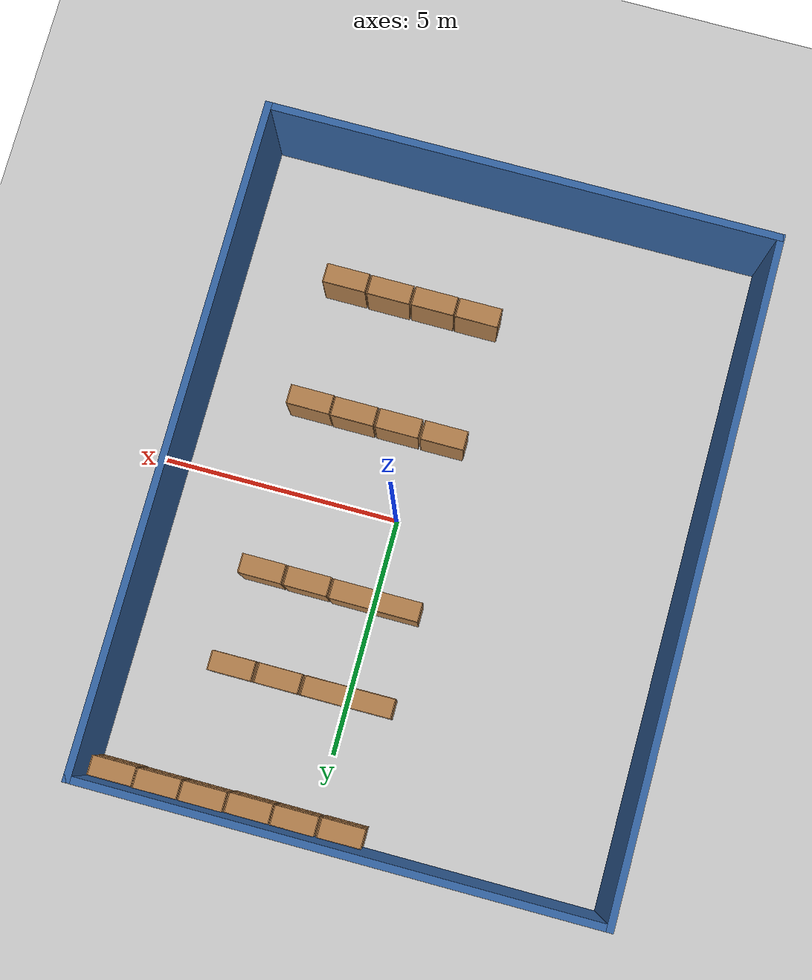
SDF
<sdf version="1.6">
 <world name="default">
  <light name="sun" type="directional">
   <pose>0 0 10 0 -0 0</pose>
   <diffuse>0.8 0.8 0.8 1</diffuse>
   <specular>0.2 0.2 0.2 1</specular>
   <attenuation>
    <range>1000</range>
    <constant>0.9</constant>
    <linear>0.01</linear>
    <quadratic>0.001</quadratic>
   </attenuation>
   <direction>-0.5 0.1 -0.9</direction>
  </light>
  <model name="ground_plane">
   <static>1</static>
   <link name="link">
    <collision name="collision">
     <geometry><plane><normal>0 0 1</normal><size>100 100</size></plane></geometry>
     <surface><friction><ode><mu>100</mu><mu2>50</mu2></ode></friction></surface>
    </collision>
    <visual name="visual">
     <cast_shadows>0</cast_shadows>
     <geometry><plane><normal>0 0 1</normal><size>100 100</size></plane></geometry>
     <material>
      <script><uri>file://media/materials/scripts/gazebo.material</uri><name>Gazebo/Grey</name></script>
     </material>
    </visual>
   </link>
  </model>
  <gravity>0 0 -9.8</gravity>
  <magnetic_field>6e-06 2.3e-05 -4.2e-05</magnetic_field>
  <atmosphere type="adiabatic"/>
  <physics name="default_physics" default="0" type="ode">
   <max_step_size>0.001</max_step_size>
   <real_time_factor>1</real_time_factor>
   <real_time_update_rate>1000</real_time_update_rate>
  </physics>
  <scene><ambient>0.4 0.4 0.4 1</ambient><background>0.7 0.7 0.7 1</background><shadows>1</shadows></scene>
  <spherical_coordinates>
   <surface_model>EARTH_WGS84</surface_model>
   <latitude_deg>0</latitude_deg>
   <longitude_deg>0</longitude_deg>
   <elevation>0</elevation>
   <heading_deg>0</heading_deg>
  </spherical_coordinates>
  <model name="blue_shop">
   <pose>-0.705855 -0.24083 0 0 -0 0</pose>
   <link name="Wall_2">
    <collision name="Wall_2_Collision">
     <geometry><box><size>10.75 0.15 2.5</size></box></geometry>
     <pose>0 0 1.25 0 -0 0</pose>
    </collision>
    <visual name="Wall_2_Visual">
     <pose>0 0 1.25 0 -0 0</pose>
     <geometry><box><size>10.75 0.15 2.5</size></box></geometry>
     <material>
      <script><uri>file://media/materials/scripts/gazebo.material</uri><name>Gazebo/Grey</name></script>
      <ambient>0.203922 0.396078 0.643137 1</ambient>
     </material>
     <meta><layer>0</layer></meta>
    </visual>
    <pose>-0 6.925 0 0 -0 3.14159</pose>
   </link>
   <link name="Wall_3">
    <collision name="Wall_3_Collision">
     <geometry><box><size>14 0.15 2.5</size></box></geometry>
     <pose>0 0 1.25 0 -0 0</pose>
    </collision>
    <visual name="Wall_3_Visual">
     <pose>0 0 1.25 0 -0 0</pose>
     <geometry><box><size>14 0.15 2.5</size></box></geometry>
     <material>
      <script><uri>file://media/materials/scripts/gazebo.material</uri><name>Gazebo/Grey</name></script>
      <ambient>0.203922 0.396078 0.643137 1</ambient>
     </material>
     <meta><layer>0</layer></meta>
    </visual>
    <pose>-5.3 0 0 0 -0 -1.5708</pose>
   </link>
   <link name="Wall_6">
    <collision name="Wall_6_Collision">
     <geometry><box><size>14 0.15 2.5</size></box></geometry>
     <pose>0 0 1.25 0 -0 0</pose>
    </collision>
    <visual name="Wall_6_Visual">
     <pose>0 0 1.25 0 -0 0</pose>
     <geometry><box><size>14 0.15 2.5</size></box></geometry>
     <material>
      <script><uri>file://media/materials/scripts/gazebo.material</uri><name>Gazebo/Grey</name></script>
      <ambient>0.203922 0.396078 0.643137 1</ambient>
     </material>
     <meta><layer>0</layer></meta>
    </visual>
    <pose>5.3 0 0 0 -0 -1.5708</pose>
   </link>
   <link name="Wall_7">
    <collision name="Wall_7_Collision">
     <geometry><box><size>10.75 0.15 2.5</size></box></geometry>
     <pose>0 0 1.25 0 -0 0</pose>
    </collision>
    <visual name="Wall_7_Visual">
     <pose>0 0 1.25 0 -0 0</pose>
     <geometry><box><size>10.75 0.15 2.5</size></box></geometry>
     <material>
      <script><uri>file://media/materials/scripts/gazebo.material</uri><name>Gazebo/Grey</name></script>
      <ambient>0.203922 0.396078 0.643137 1</ambient>
     </material>
     <meta><layer>0</layer></meta>
    </visual>
    <pose>-0 -6.925 0 0 -0 3.14159</pose>
   </link>
   <static>1</static>
  </model>
  <model name="bookshelf">
   <static>1</static>
   <link name="link">
    <inertial><mass>1</mass></inertial>
    <collision name="back">
     <pose>0 0.005 0.6 0 -0 0</pose>
     <geometry><box><size>0.9 0.01 1.2</size></box></geometry>
    </collision>
    <visual name="visual1">
     <pose>0 0.005 0.6 0 -0 0</pose>
     <geometry><box><size>0.9 0.01 1.2</size></box></geometry>
     <material>
      <script><uri>file://media/materials/scripts/gazebo.material</uri><name>Gazebo/Wood</name></script>
     </material>
    </visual>
    <collision name="left_side">
     <pose>0.45 -0.195 0.6 0 -0 0</pose>
     <geometry><box><size>0.02 0.4 1.2</size></box></geometry>
    </collision>
    <visual name="visual2">
     <pose>0.45 -0.195 0.6 0 -0 0</pose>
     <geometry><box><size>0.02 0.4 1.2</size></box></geometry>
     <material>
      <script><uri>file://media/materials/scripts/gazebo.material</uri><name>Gazebo/Wood</name></script>
     </material>
    </visual>
    <collision name="right_side">
     <pose>-0.45 -0.195 0.6 0 -0 0</pose>
     <geometry><box><size>0.02 0.4 1.2</size></box></geometry>
    </collision>
    <visual name="visual3">
     <pose>-0.45 -0.195 0.6 0 -0 0</pose>
     <geometry><box><size>0.02 0.4 1.2</size></box></geometry>
     <material>
      <script><uri>file://media/materials/scripts/gazebo.material</uri><name>Gazebo/Wood</name></script>
     </material>
    </visual>
    <collision name="bottom">
     <pose>0 -0.195 0.03 0 -0 0</pose>
     <geometry><box><size>0.88 0.4 0.06</size></box></geometry>
    </collision>
    <visual name="visual4">
     <pose>0 -0.195 0.03 0 -0 0</pose>
     <geometry><box><size>0.88 0.4 0.06</size></box></geometry>
     <material>
      <script><uri>file://media/materials/scripts/gazebo.material</uri><name>Gazebo/Wood</name></script>
     </material>
    </visual>
    <collision name="top">
     <pose>0 -0.195 1.19 0 -0 0</pose>
     <geometry><box><size>0.88 0.4 0.02</size></box></geometry>
    </collision>
    <visual name="visual5">
     <pose>0 -0.195 1.19 0 -0 0</pose>
     <geometry><box><size>0.88 0.4 0.02</size></box></geometry>
     <material>
      <script><uri>file://media/materials/scripts/gazebo.material</uri><name>Gazebo/Wood</name></script>
     </material>
    </visual>
    <collision name="low_shelf">
     <pose>0 -0.195 0.43 0 -0 0</pose>
     <geometry><box><size>0.88 0.4 0.02</size></box></geometry>
    </collision>
    <visual name="visual6">
     <pose>0 -0.195 0.43 0 -0 0</pose>
     <geometry><box><size>0.88 0.4 0.02</size></box></geometry>
     <material>
      <script><uri>file://media/materials/scripts/gazebo.material</uri><name>Gazebo/Wood</name></script>
     </material>
    </visual>
    <collision name="high_shelf">
     <pose>0 -0.195 0.8 0 -0 0</pose>
     <geometry><box><size>0.88 0.4 0.02</size></box></geometry>
    </collision>
    <visual name="visual7">
     <pose>0 -0.195 0.8 0 -0 0</pose>
     <geometry><box><size>0.88 0.4 0.02</size></box></geometry>
     <material>
      <script><uri>file://media/materials/scripts/gazebo.material</uri><name>Gazebo/Wood</name></script>
     </material>
    </visual>
   </link>
   <pose>4.05709 6.59191 0 0 -0 0</pose>
  </model>
  <model name="bookshelf_0">
   <static>1</static>
   <link name="link">
    <inertial><mass>1</mass></inertial>
    <collision name="back">
     <pose>0 0.005 0.6 0 -0 0</pose>
     <geometry><box><size>0.9 0.01 1.2</size></box></geometry>
    </collision>
    <visual name="visual1">
     <pose>0 0.005 0.6 0 -0 0</pose>
     <geometry><box><size>0.9 0.01 1.2</size></box></geometry>
     <material>
      <script><uri>file://media/materials/scripts/gazebo.material</uri><name>Gazebo/Wood</name></script>
     </material>
    </visual>
    <collision name="left_side">
     <pose>0.45 -0.195 0.6 0 -0 0</pose>
     <geometry><box><size>0.02 0.4 1.2</size></box></geometry>
    </collision>
    <visual name="visual2">
     <pose>0.45 -0.195 0.6 0 -0 0</pose>
     <geometry><box><size>0.02 0.4 1.2</size></box></geometry>
     <material>
      <script><uri>file://media/materials/scripts/gazebo.material</uri><name>Gazebo/Wood</name></script>
     </material>
    </visual>
    <collision name="right_side">
     <pose>-0.45 -0.195 0.6 0 -0 0</pose>
     <geometry><box><size>0.02 0.4 1.2</size></box></geometry>
    </collision>
    <visual name="visual3">
     <pose>-0.45 -0.195 0.6 0 -0 0</pose>
     <geometry><box><size>0.02 0.4 1.2</size></box></geometry>
     <material>
      <script><uri>file://media/materials/scripts/gazebo.material</uri><name>Gazebo/Wood</name></script>
     </material>
    </visual>
    <collision name="bottom">
     <pose>0 -0.195 0.03 0 -0 0</pose>
     <geometry><box><size>0.88 0.4 0.06</size></box></geometry>
    </collision>
    <visual name="visual4">
     <pose>0 -0.195 0.03 0 -0 0</pose>
     <geometry><box><size>0.88 0.4 0.06</size></box></geometry>
     <material>
      <script><uri>file://media/materials/scripts/gazebo.material</uri><name>Gazebo/Wood</name></script>
     </material>
    </visual>
    <collision name="top">
     <pose>0 -0.195 1.19 0 -0 0</pose>
     <geometry><box><size>0.88 0.4 0.02</size></box></geometry>
    </collision>
    <visual name="visual5">
     <pose>0 -0.195 1.19 0 -0 0</pose>
     <geometry><box><size>0.88 0.4 0.02</size></box></geometry>
     <material>
      <script><uri>file://media/materials/scripts/gazebo.material</uri><name>Gazebo/Wood</name></script>
     </material>
    </visual>
    <collision name="low_shelf">
     <pose>0 -0.195 0.43 0 -0 0</pose>
     <geometry><box><size>0.88 0.4 0.02</size></box></geometry>
    </collision>
    <visual name="visual6">
     <pose>0 -0.195 0.43 0 -0 0</pose>
     <geometry><box><size>0.88 0.4 0.02</size></box></geometry>
     <material>
      <script><uri>file://media/materials/scripts/gazebo.material</uri><name>Gazebo/Wood</name></script>
     </material>
    </visual>
    <collision name="high_shelf">
     <pose>0 -0.195 0.8 0 -0 0</pose>
     <geometry><box><size>0.88 0.4 0.02</size></box></geometry>
    </collision>
    <visual name="visual7">
     <pose>0 -0.195 0.8 0 -0 0</pose>
     <geometry><box><size>0.88 0.4 0.02</size></box></geometry>
     <material>
      <script><uri>file://media/materials/scripts/gazebo.material</uri><name>Gazebo/Wood</name></script>
     </material>
    </visual>
   </link>
   <pose>3.12879 6.60173 0 0 -0 0</pose>
  </model>
  <model name="bookshelf_1">
   <static>1</static>
   <link name="link">
    <inertial><mass>1</mass></inertial>
    <collision name="back">
     <pose>0 0.005 0.6 0 -0 0</pose>
     <geometry><box><size>0.9 0.01 1.2</size></box></geometry>
    </collision>
    <visual name="visual1">
     <pose>0 0.005 0.6 0 -0 0</pose>
     <geometry><box><size>0.9 0.01 1.2</size></box></geometry>
     <material>
      <script><uri>file://media/materials/scripts/gazebo.material</uri><name>Gazebo/Wood</name></script>
     </material>
    </visual>
    <collision name="left_side">
     <pose>0.45 -0.195 0.6 0 -0 0</pose>
     <geometry><box><size>0.02 0.4 1.2</size></box></geometry>
    </collision>
    <visual name="visual2">
     <pose>0.45 -0.195 0.6 0 -0 0</pose>
     <geometry><box><size>0.02 0.4 1.2</size></box></geometry>
     <material>
      <script><uri>file://media/materials/scripts/gazebo.material</uri><name>Gazebo/Wood</name></script>
     </material>
    </visual>
    <collision name="right_side">
     <pose>-0.45 -0.195 0.6 0 -0 0</pose>
     <geometry><box><size>0.02 0.4 1.2</size></box></geometry>
    </collision>
    <visual name="visual3">
     <pose>-0.45 -0.195 0.6 0 -0 0</pose>
     <geometry><box><size>0.02 0.4 1.2</size></box></geometry>
     <material>
      <script><uri>file://media/materials/scripts/gazebo.material</uri><name>Gazebo/Wood</name></script>
     </material>
    </visual>
    <collision name="bottom">
     <pose>0 -0.195 0.03 0 -0 0</pose>
     <geometry><box><size>0.88 0.4 0.06</size></box></geometry>
    </collision>
    <visual name="visual4">
     <pose>0 -0.195 0.03 0 -0 0</pose>
     <geometry><box><size>0.88 0.4 0.06</size></box></geometry>
     <material>
      <script><uri>file://media/materials/scripts/gazebo.material</uri><name>Gazebo/Wood</name></script>
     </material>
    </visual>
    <collision name="top">
     <pose>0 -0.195 1.19 0 -0 0</pose>
     <geometry><box><size>0.88 0.4 0.02</size></box></geometry>
    </collision>
    <visual name="visual5">
     <pose>0 -0.195 1.19 0 -0 0</pose>
     <geometry><box><size>0.88 0.4 0.02</size></box></geometry>
     <material>
      <script><uri>file://media/materials/scripts/gazebo.material</uri><name>Gazebo/Wood</name></script>
     </material>
    </visual>
    <collision name="low_shelf">
     <pose>0 -0.195 0.43 0 -0 0</pose>
     <geometry><box><size>0.88 0.4 0.02</size></box></geometry>
    </collision>
    <visual name="visual6">
     <pose>0 -0.195 0.43 0 -0 0</pose>
     <geometry><box><size>0.88 0.4 0.02</size></box></geometry>
     <material>
      <script><uri>file://media/materials/scripts/gazebo.material</uri><name>Gazebo/Wood</name></script>
     </material>
    </visual>
    <collision name="high_shelf">
     <pose>0 -0.195 0.8 0 -0 0</pose>
     <geometry><box><size>0.88 0.4 0.02</size></box></geometry>
    </collision>
    <visual name="visual7">
     <pose>0 -0.195 0.8 0 -0 0</pose>
     <geometry><box><size>0.88 0.4 0.02</size></box></geometry>
     <material>
      <script><uri>file://media/materials/scripts/gazebo.material</uri><name>Gazebo/Wood</name></script>
     </material>
    </visual>
   </link>
   <pose>2.19452 6.60359 0 0 -0 0</pose>
  </model>
  <model name="bookshelf_2">
   <static>1</static>
   <link name="link">
    <inertial><mass>1</mass></inertial>
    <collision name="back">
     <pose>0 0.005 0.6 0 -0 0</pose>
     <geometry><box><size>0.9 0.01 1.2</size></box></geometry>
    </collision>
    <visual name="visual1">
     <pose>0 0.005 0.6 0 -0 0</pose>
     <geometry><box><size>0.9 0.01 1.2</size></box></geometry>
     <material>
      <script><uri>file://media/materials/scripts/gazebo.material</uri><name>Gazebo/Wood</name></script>
     </material>
    </visual>
    <collision name="left_side">
     <pose>0.45 -0.195 0.6 0 -0 0</pose>
     <geometry><box><size>0.02 0.4 1.2</size></box></geometry>
    </collision>
    <visual name="visual2">
     <pose>0.45 -0.195 0.6 0 -0 0</pose>
     <geometry><box><size>0.02 0.4 1.2</size></box></geometry>
     <material>
      <script><uri>file://media/materials/scripts/gazebo.material</uri><name>Gazebo/Wood</name></script>
     </material>
    </visual>
    <collision name="right_side">
     <pose>-0.45 -0.195 0.6 0 -0 0</pose>
     <geometry><box><size>0.02 0.4 1.2</size></box></geometry>
    </collision>
    <visual name="visual3">
     <pose>-0.45 -0.195 0.6 0 -0 0</pose>
     <geometry><box><size>0.02 0.4 1.2</size></box></geometry>
     <material>
      <script><uri>file://media/materials/scripts/gazebo.material</uri><name>Gazebo/Wood</name></script>
     </material>
    </visual>
    <collision name="bottom">
     <pose>0 -0.195 0.03 0 -0 0</pose>
     <geometry><box><size>0.88 0.4 0.06</size></box></geometry>
    </collision>
    <visual name="visual4">
     <pose>0 -0.195 0.03 0 -0 0</pose>
     <geometry><box><size>0.88 0.4 0.06</size></box></geometry>
     <material>
      <script><uri>file://media/materials/scripts/gazebo.material</uri><name>Gazebo/Wood</name></script>
     </material>
    </visual>
    <collision name="top">
     <pose>0 -0.195 1.19 0 -0 0</pose>
     <geometry><box><size>0.88 0.4 0.02</size></box></geometry>
    </collision>
    <visual name="visual5">
     <pose>0 -0.195 1.19 0 -0 0</pose>
     <geometry><box><size>0.88 0.4 0.02</size></box></geometry>
     <material>
      <script><uri>file://media/materials/scripts/gazebo.material</uri><name>Gazebo/Wood</name></script>
     </material>
    </visual>
    <collision name="low_shelf">
     <pose>0 -0.195 0.43 0 -0 0</pose>
     <geometry><box><size>0.88 0.4 0.02</size></box></geometry>
    </collision>
    <visual name="visual6">
     <pose>0 -0.195 0.43 0 -0 0</pose>
     <geometry><box><size>0.88 0.4 0.02</size></box></geometry>
     <material>
      <script><uri>file://media/materials/scripts/gazebo.material</uri><name>Gazebo/Wood</name></script>
     </material>
    </visual>
    <collision name="high_shelf">
     <pose>0 -0.195 0.8 0 -0 0</pose>
     <geometry><box><size>0.88 0.4 0.02</size></box></geometry>
    </collision>
    <visual name="visual7">
     <pose>0 -0.195 0.8 0 -0 0</pose>
     <geometry><box><size>0.88 0.4 0.02</size></box></geometry>
     <material>
      <script><uri>file://media/materials/scripts/gazebo.material</uri><name>Gazebo/Wood</name></script>
     </material>
    </visual>
   </link>
   <pose>1.25194 6.58848 0 0 -0 0</pose>
  </model>
  <model name="bookshelf_3">
   <static>1</static>
   <link name="link">
    <inertial><mass>1</mass></inertial>
    <collision name="back">
     <pose>0 0.005 0.6 0 -0 0</pose>
     <geometry><box><size>0.9 0.01 1.2</size></box></geometry>
    </collision>
    <visual name="visual1">
     <pose>0 0.005 0.6 0 -0 0</pose>
     <geometry><box><size>0.9 0.01 1.2</size></box></geometry>
     <material>
      <script><uri>file://media/materials/scripts/gazebo.material</uri><name>Gazebo/Wood</name></script>
     </material>
    </visual>
    <collision name="left_side">
     <pose>0.45 -0.195 0.6 0 -0 0</pose>
     <geometry><box><size>0.02 0.4 1.2</size></box></geometry>
    </collision>
    <visual name="visual2">
     <pose>0.45 -0.195 0.6 0 -0 0</pose>
     <geometry><box><size>0.02 0.4 1.2</size></box></geometry>
     <material>
      <script><uri>file://media/materials/scripts/gazebo.material</uri><name>Gazebo/Wood</name></script>
     </material>
    </visual>
    <collision name="right_side">
     <pose>-0.45 -0.195 0.6 0 -0 0</pose>
     <geometry><box><size>0.02 0.4 1.2</size></box></geometry>
    </collision>
    <visual name="visual3">
     <pose>-0.45 -0.195 0.6 0 -0 0</pose>
     <geometry><box><size>0.02 0.4 1.2</size></box></geometry>
     <material>
      <script><uri>file://media/materials/scripts/gazebo.material</uri><name>Gazebo/Wood</name></script>
     </material>
    </visual>
    <collision name="bottom">
     <pose>0 -0.195 0.03 0 -0 0</pose>
     <geometry><box><size>0.88 0.4 0.06</size></box></geometry>
    </collision>
    <visual name="visual4">
     <pose>0 -0.195 0.03 0 -0 0</pose>
     <geometry><box><size>0.88 0.4 0.06</size></box></geometry>
     <material>
      <script><uri>file://media/materials/scripts/gazebo.material</uri><name>Gazebo/Wood</name></script>
     </material>
    </visual>
    <collision name="top">
     <pose>0 -0.195 1.19 0 -0 0</pose>
     <geometry><box><size>0.88 0.4 0.02</size></box></geometry>
    </collision>
    <visual name="visual5">
     <pose>0 -0.195 1.19 0 -0 0</pose>
     <geometry><box><size>0.88 0.4 0.02</size></box></geometry>
     <material>
      <script><uri>file://media/materials/scripts/gazebo.material</uri><name>Gazebo/Wood</name></script>
     </material>
    </visual>
    <collision name="low_shelf">
     <pose>0 -0.195 0.43 0 -0 0</pose>
     <geometry><box><size>0.88 0.4 0.02</size></box></geometry>
    </collision>
    <visual name="visual6">
     <pose>0 -0.195 0.43 0 -0 0</pose>
     <geometry><box><size>0.88 0.4 0.02</size></box></geometry>
     <material>
      <script><uri>file://media/materials/scripts/gazebo.material</uri><name>Gazebo/Wood</name></script>
     </material>
    </visual>
    <collision name="high_shelf">
     <pose>0 -0.195 0.8 0 -0 0</pose>
     <geometry><box><size>0.88 0.4 0.02</size></box></geometry>
    </collision>
    <visual name="visual7">
     <pose>0 -0.195 0.8 0 -0 0</pose>
     <geometry><box><size>0.88 0.4 0.02</size></box></geometry>
     <material>
      <script><uri>file://media/materials/scripts/gazebo.material</uri><name>Gazebo/Wood</name></script>
     </material>
    </visual>
   </link>
   <pose>0.319104 6.58896 0 0 -0 0</pose>
  </model>
  <model name="bookshelf_4">
   <static>1</static>
   <link name="link">
    <inertial><mass>1</mass></inertial>
    <collision name="back">
     <pose>0 0.005 0.6 0 -0 0</pose>
     <geometry><box><size>0.9 0.01 1.2</size></box></geometry>
    </collision>
    <visual name="visual1">
     <pose>0 0.005 0.6 0 -0 0</pose>
     <geometry><box><size>0.9 0.01 1.2</size></box></geometry>
     <material>
      <script><uri>file://media/materials/scripts/gazebo.material</uri><name>Gazebo/Wood</name></script>
     </material>
    </visual>
    <collision name="left_side">
     <pose>0.45 -0.195 0.6 0 -0 0</pose>
     <geometry><box><size>0.02 0.4 1.2</size></box></geometry>
    </collision>
    <visual name="visual2">
     <pose>0.45 -0.195 0.6 0 -0 0</pose>
     <geometry><box><size>0.02 0.4 1.2</size></box></geometry>
     <material>
      <script><uri>file://media/materials/scripts/gazebo.material</uri><name>Gazebo/Wood</name></script>
     </material>
    </visual>
    <collision name="right_side">
     <pose>-0.45 -0.195 0.6 0 -0 0</pose>
     <geometry><box><size>0.02 0.4 1.2</size></box></geometry>
    </collision>
    <visual name="visual3">
     <pose>-0.45 -0.195 0.6 0 -0 0</pose>
     <geometry><box><size>0.02 0.4 1.2</size></box></geometry>
     <material>
      <script><uri>file://media/materials/scripts/gazebo.material</uri><name>Gazebo/Wood</name></script>
     </material>
    </visual>
    <collision name="bottom">
     <pose>0 -0.195 0.03 0 -0 0</pose>
     <geometry><box><size>0.88 0.4 0.06</size></box></geometry>
    </collision>
    <visual name="visual4">
     <pose>0 -0.195 0.03 0 -0 0</pose>
     <geometry><box><size>0.88 0.4 0.06</size></box></geometry>
     <material>
      <script><uri>file://media/materials/scripts/gazebo.material</uri><name>Gazebo/Wood</name></script>
     </material>
    </visual>
    <collision name="top">
     <pose>0 -0.195 1.19 0 -0 0</pose>
     <geometry><box><size>0.88 0.4 0.02</size></box></geometry>
    </collision>
    <visual name="visual5">
     <pose>0 -0.195 1.19 0 -0 0</pose>
     <geometry><box><size>0.88 0.4 0.02</size></box></geometry>
     <material>
      <script><uri>file://media/materials/scripts/gazebo.material</uri><name>Gazebo/Wood</name></script>
     </material>
    </visual>
    <collision name="low_shelf">
     <pose>0 -0.195 0.43 0 -0 0</pose>
     <geometry><box><size>0.88 0.4 0.02</size></box></geometry>
    </collision>
    <visual name="visual6">
     <pose>0 -0.195 0.43 0 -0 0</pose>
     <geometry><box><size>0.88 0.4 0.02</size></box></geometry>
     <material>
      <script><uri>file://media/materials/scripts/gazebo.material</uri><name>Gazebo/Wood</name></script>
     </material>
    </visual>
    <collision name="high_shelf">
     <pose>0 -0.195 0.8 0 -0 0</pose>
     <geometry><box><size>0.88 0.4 0.02</size></box></geometry>
    </collision>
    <visual name="visual7">
     <pose>0 -0.195 0.8 0 -0 0</pose>
     <geometry><box><size>0.88 0.4 0.02</size></box></geometry>
     <material>
      <script><uri>file://media/materials/scripts/gazebo.material</uri><name>Gazebo/Wood</name></script>
     </material>
    </visual>
   </link>
   <pose>-0.528232 3.59496 0 0 0 -3.13715</pose>
  </model>
  <model name="bookshelf_5">
   <static>1</static>
   <link name="link">
    <inertial><mass>1</mass></inertial>
    <collision name="back">
     <pose>0 0.005 0.6 0 -0 0</pose>
     <geometry><box><size>0.9 0.01 1.2</size></box></geometry>
    </collision>
    <visual name="visual1">
     <pose>0 0.005 0.6 0 -0 0</pose>
     <geometry><box><size>0.9 0.01 1.2</size></box></geometry>
     <material>
      <script><uri>file://media/materials/scripts/gazebo.material</uri><name>Gazebo/Wood</name></script>
     </material>
    </visual>
    <collision name="left_side">
     <pose>0.45 -0.195 0.6 0 -0 0</pose>
     <geometry><box><size>0.02 0.4 1.2</size></box></geometry>
    </collision>
    <visual name="visual2">
     <pose>0.45 -0.195 0.6 0 -0 0</pose>
     <geometry><box><size>0.02 0.4 1.2</size></box></geometry>
     <material>
      <script><uri>file://media/materials/scripts/gazebo.material</uri><name>Gazebo/Wood</name></script>
     </material>
    </visual>
    <collision name="right_side">
     <pose>-0.45 -0.195 0.6 0 -0 0</pose>
     <geometry><box><size>0.02 0.4 1.2</size></box></geometry>
    </collision>
    <visual name="visual3">
     <pose>-0.45 -0.195 0.6 0 -0 0</pose>
     <geometry><box><size>0.02 0.4 1.2</size></box></geometry>
     <material>
      <script><uri>file://media/materials/scripts/gazebo.material</uri><name>Gazebo/Wood</name></script>
     </material>
    </visual>
    <collision name="bottom">
     <pose>0 -0.195 0.03 0 -0 0</pose>
     <geometry><box><size>0.88 0.4 0.06</size></box></geometry>
    </collision>
    <visual name="visual4">
     <pose>0 -0.195 0.03 0 -0 0</pose>
     <geometry><box><size>0.88 0.4 0.06</size></box></geometry>
     <material>
      <script><uri>file://media/materials/scripts/gazebo.material</uri><name>Gazebo/Wood</name></script>
     </material>
    </visual>
    <collision name="top">
     <pose>0 -0.195 1.19 0 -0 0</pose>
     <geometry><box><size>0.88 0.4 0.02</size></box></geometry>
    </collision>
    <visual name="visual5">
     <pose>0 -0.195 1.19 0 -0 0</pose>
     <geometry><box><size>0.88 0.4 0.02</size></box></geometry>
     <material>
      <script><uri>file://media/materials/scripts/gazebo.material</uri><name>Gazebo/Wood</name></script>
     </material>
    </visual>
    <collision name="low_shelf">
     <pose>0 -0.195 0.43 0 -0 0</pose>
     <geometry><box><size>0.88 0.4 0.02</size></box></geometry>
    </collision>
    <visual name="visual6">
     <pose>0 -0.195 0.43 0 -0 0</pose>
     <geometry><box><size>0.88 0.4 0.02</size></box></geometry>
     <material>
      <script><uri>file://media/materials/scripts/gazebo.material</uri><name>Gazebo/Wood</name></script>
     </material>
    </visual>
    <collision name="high_shelf">
     <pose>0 -0.195 0.8 0 -0 0</pose>
     <geometry><box><size>0.88 0.4 0.02</size></box></geometry>
    </collision>
    <visual name="visual7">
     <pose>0 -0.195 0.8 0 -0 0</pose>
     <geometry><box><size>0.88 0.4 0.02</size></box></geometry>
     <material>
      <script><uri>file://media/materials/scripts/gazebo.material</uri><name>Gazebo/Wood</name></script>
     </material>
    </visual>
   </link>
   <pose>0.427849 3.60204 0 0 0 -3.14074</pose>
  </model>
  <model name="bookshelf_6">
   <static>1</static>
   <link name="link">
    <inertial><mass>1</mass></inertial>
    <collision name="back">
     <pose>0 0.005 0.6 0 -0 0</pose>
     <geometry><box><size>0.9 0.01 1.2</size></box></geometry>
    </collision>
    <visual name="visual1">
     <pose>0 0.005 0.6 0 -0 0</pose>
     <geometry><box><size>0.9 0.01 1.2</size></box></geometry>
     <material>
      <script><uri>file://media/materials/scripts/gazebo.material</uri><name>Gazebo/Wood</name></script>
     </material>
    </visual>
    <collision name="left_side">
     <pose>0.45 -0.195 0.6 0 -0 0</pose>
     <geometry><box><size>0.02 0.4 1.2</size></box></geometry>
    </collision>
    <visual name="visual2">
     <pose>0.45 -0.195 0.6 0 -0 0</pose>
     <geometry><box><size>0.02 0.4 1.2</size></box></geometry>
     <material>
      <script><uri>file://media/materials/scripts/gazebo.material</uri><name>Gazebo/Wood</name></script>
     </material>
    </visual>
    <collision name="right_side">
     <pose>-0.45 -0.195 0.6 0 -0 0</pose>
     <geometry><box><size>0.02 0.4 1.2</size></box></geometry>
    </collision>
    <visual name="visual3">
     <pose>-0.45 -0.195 0.6 0 -0 0</pose>
     <geometry><box><size>0.02 0.4 1.2</size></box></geometry>
     <material>
      <script><uri>file://media/materials/scripts/gazebo.material</uri><name>Gazebo/Wood</name></script>
     </material>
    </visual>
    <collision name="bottom">
     <pose>0 -0.195 0.03 0 -0 0</pose>
     <geometry><box><size>0.88 0.4 0.06</size></box></geometry>
    </collision>
    <visual name="visual4">
     <pose>0 -0.195 0.03 0 -0 0</pose>
     <geometry><box><size>0.88 0.4 0.06</size></box></geometry>
     <material>
      <script><uri>file://media/materials/scripts/gazebo.material</uri><name>Gazebo/Wood</name></script>
     </material>
    </visual>
    <collision name="top">
     <pose>0 -0.195 1.19 0 -0 0</pose>
     <geometry><box><size>0.88 0.4 0.02</size></box></geometry>
    </collision>
    <visual name="visual5">
     <pose>0 -0.195 1.19 0 -0 0</pose>
     <geometry><box><size>0.88 0.4 0.02</size></box></geometry>
     <material>
      <script><uri>file://media/materials/scripts/gazebo.material</uri><name>Gazebo/Wood</name></script>
     </material>
    </visual>
    <collision name="low_shelf">
     <pose>0 -0.195 0.43 0 -0 0</pose>
     <geometry><box><size>0.88 0.4 0.02</size></box></geometry>
    </collision>
    <visual name="visual6">
     <pose>0 -0.195 0.43 0 -0 0</pose>
     <geometry><box><size>0.88 0.4 0.02</size></box></geometry>
     <material>
      <script><uri>file://media/materials/scripts/gazebo.material</uri><name>Gazebo/Wood</name></script>
     </material>
    </visual>
    <collision name="high_shelf">
     <pose>0 -0.195 0.8 0 -0 0</pose>
     <geometry><box><size>0.88 0.4 0.02</size></box></geometry>
    </collision>
    <visual name="visual7">
     <pose>0 -0.195 0.8 0 -0 0</pose>
     <geometry><box><size>0.88 0.4 0.02</size></box></geometry>
     <material>
      <script><uri>file://media/materials/scripts/gazebo.material</uri><name>Gazebo/Wood</name></script>
     </material>
    </visual>
   </link>
   <pose>1.38749 3.60149 0 0 -0 3.14021</pose>
  </model>
  <model name="bookshelf_7">
   <static>1</static>
   <link name="link">
    <inertial><mass>1</mass></inertial>
    <collision name="back">
     <pose>0 0.005 0.6 0 -0 0</pose>
     <geometry><box><size>0.9 0.01 1.2</size></box></geometry>
    </collision>
    <visual name="visual1">
     <pose>0 0.005 0.6 0 -0 0</pose>
     <geometry><box><size>0.9 0.01 1.2</size></box></geometry>
     <material>
      <script><uri>file://media/materials/scripts/gazebo.material</uri><name>Gazebo/Wood</name></script>
     </material>
    </visual>
    <collision name="left_side">
     <pose>0.45 -0.195 0.6 0 -0 0</pose>
     <geometry><box><size>0.02 0.4 1.2</size></box></geometry>
    </collision>
    <visual name="visual2">
     <pose>0.45 -0.195 0.6 0 -0 0</pose>
     <geometry><box><size>0.02 0.4 1.2</size></box></geometry>
     <material>
      <script><uri>file://media/materials/scripts/gazebo.material</uri><name>Gazebo/Wood</name></script>
     </material>
    </visual>
    <collision name="right_side">
     <pose>-0.45 -0.195 0.6 0 -0 0</pose>
     <geometry><box><size>0.02 0.4 1.2</size></box></geometry>
    </collision>
    <visual name="visual3">
     <pose>-0.45 -0.195 0.6 0 -0 0</pose>
     <geometry><box><size>0.02 0.4 1.2</size></box></geometry>
     <material>
      <script><uri>file://media/materials/scripts/gazebo.material</uri><name>Gazebo/Wood</name></script>
     </material>
    </visual>
    <collision name="bottom">
     <pose>0 -0.195 0.03 0 -0 0</pose>
     <geometry><box><size>0.88 0.4 0.06</size></box></geometry>
    </collision>
    <visual name="visual4">
     <pose>0 -0.195 0.03 0 -0 0</pose>
     <geometry><box><size>0.88 0.4 0.06</size></box></geometry>
     <material>
      <script><uri>file://media/materials/scripts/gazebo.material</uri><name>Gazebo/Wood</name></script>
     </material>
    </visual>
    <collision name="top">
     <pose>0 -0.195 1.19 0 -0 0</pose>
     <geometry><box><size>0.88 0.4 0.02</size></box></geometry>
    </collision>
    <visual name="visual5">
     <pose>0 -0.195 1.19 0 -0 0</pose>
     <geometry><box><size>0.88 0.4 0.02</size></box></geometry>
     <material>
      <script><uri>file://media/materials/scripts/gazebo.material</uri><name>Gazebo/Wood</name></script>
     </material>
    </visual>
    <collision name="low_shelf">
     <pose>0 -0.195 0.43 0 -0 0</pose>
     <geometry><box><size>0.88 0.4 0.02</size></box></geometry>
    </collision>
    <visual name="visual6">
     <pose>0 -0.195 0.43 0 -0 0</pose>
     <geometry><box><size>0.88 0.4 0.02</size></box></geometry>
     <material>
      <script><uri>file://media/materials/scripts/gazebo.material</uri><name>Gazebo/Wood</name></script>
     </material>
    </visual>
    <collision name="high_shelf">
     <pose>0 -0.195 0.8 0 -0 0</pose>
     <geometry><box><size>0.88 0.4 0.02</size></box></geometry>
    </collision>
    <visual name="visual7">
     <pose>0 -0.195 0.8 0 -0 0</pose>
     <geometry><box><size>0.88 0.4 0.02</size></box></geometry>
     <material>
      <script><uri>file://media/materials/scripts/gazebo.material</uri><name>Gazebo/Wood</name></script>
     </material>
    </visual>
   </link>
   <pose>2.35348 3.60082 0 0 0 -3.1389</pose>
  </model>
  <model name="bookshelf_3_clone">
   <static>1</static>
   <link name="link">
    <inertial><mass>1</mass></inertial>
    <collision name="back">
     <pose>0 0.005 0.6 0 -0 0</pose>
     <geometry><box><size>0.9 0.01 1.2</size></box></geometry>
    </collision>
    <visual name="visual1">
     <pose>0 0.005 0.6 0 -0 0</pose>
     <geometry><box><size>0.9 0.01 1.2</size></box></geometry>
     <material>
      <script><uri>file://media/materials/scripts/gazebo.material</uri><name>Gazebo/Wood</name></script>
     </material>
    </visual>
    <collision name="left_side">
     <pose>0.45 -0.195 0.6 0 -0 0</pose>
     <geometry><box><size>0.02 0.4 1.2</size></box></geometry>
    </collision>
    <visual name="visual2">
     <pose>0.45 -0.195 0.6 0 -0 0</pose>
     <geometry><box><size>0.02 0.4 1.2</size></box></geometry>
     <material>
      <script><uri>file://media/materials/scripts/gazebo.material</uri><name>Gazebo/Wood</name></script>
     </material>
    </visual>
    <collision name="right_side">
     <pose>-0.45 -0.195 0.6 0 -0 0</pose>
     <geometry><box><size>0.02 0.4 1.2</size></box></geometry>
    </collision>
    <visual name="visual3">
     <pose>-0.45 -0.195 0.6 0 -0 0</pose>
     <geometry><box><size>0.02 0.4 1.2</size></box></geometry>
     <material>
      <script><uri>file://media/materials/scripts/gazebo.material</uri><name>Gazebo/Wood</name></script>
     </material>
    </visual>
    <collision name="bottom">
     <pose>0 -0.195 0.03 0 -0 0</pose>
     <geometry><box><size>0.88 0.4 0.06</size></box></geometry>
    </collision>
    <visual name="visual4">
     <pose>0 -0.195 0.03 0 -0 0</pose>
     <geometry><box><size>0.88 0.4 0.06</size></box></geometry>
     <material>
      <script><uri>file://media/materials/scripts/gazebo.material</uri><name>Gazebo/Wood</name></script>
     </material>
    </visual>
    <collision name="top">
     <pose>0 -0.195 1.19 0 -0 0</pose>
     <geometry><box><size>0.88 0.4 0.02</size></box></geometry>
    </collision>
    <visual name="visual5">
     <pose>0 -0.195 1.19 0 -0 0</pose>
     <geometry><box><size>0.88 0.4 0.02</size></box></geometry>
     <material>
      <script><uri>file://media/materials/scripts/gazebo.material</uri><name>Gazebo/Wood</name></script>
     </material>
    </visual>
    <collision name="low_shelf">
     <pose>0 -0.195 0.43 0 -0 0</pose>
     <geometry><box><size>0.88 0.4 0.02</size></box></geometry>
    </collision>
    <visual name="visual6">
     <pose>0 -0.195 0.43 0 -0 0</pose>
     <geometry><box><size>0.88 0.4 0.02</size></box></geometry>
     <material>
      <script><uri>file://media/materials/scripts/gazebo.material</uri><name>Gazebo/Wood</name></script>
     </material>
    </visual>
    <collision name="high_shelf">
     <pose>0 -0.195 0.8 0 -0 0</pose>
     <geometry><box><size>0.88 0.4 0.02</size></box></geometry>
    </collision>
    <visual name="visual7">
     <pose>0 -0.195 0.8 0 -0 0</pose>
     <geometry><box><size>0.88 0.4 0.02</size></box></geometry>
     <material>
      <script><uri>file://media/materials/scripts/gazebo.material</uri><name>Gazebo/Wood</name></script>
     </material>
    </visual>
   </link>
   <pose>-0.546107 1.99716 0 0 -0 0</pose>
  </model>
  <model name="bookshelf_3_clone_0">
   <static>1</static>
   <link name="link">
    <inertial><mass>1</mass></inertial>
    <collision name="back">
     <pose>0 0.005 0.6 0 -0 0</pose>
     <geometry><box><size>0.9 0.01 1.2</size></box></geometry>
    </collision>
    <visual name="visual1">
     <pose>0 0.005 0.6 0 -0 0</pose>
     <geometry><box><size>0.9 0.01 1.2</size></box></geometry>
     <material>
      <script><uri>file://media/materials/scripts/gazebo.material</uri><name>Gazebo/Wood</name></script>
     </material>
    </visual>
    <collision name="left_side">
     <pose>0.45 -0.195 0.6 0 -0 0</pose>
     <geometry><box><size>0.02 0.4 1.2</size></box></geometry>
    </collision>
    <visual name="visual2">
     <pose>0.45 -0.195 0.6 0 -0 0</pose>
     <geometry><box><size>0.02 0.4 1.2</size></box></geometry>
     <material>
      <script><uri>file://media/materials/scripts/gazebo.material</uri><name>Gazebo/Wood</name></script>
     </material>
    </visual>
    <collision name="right_side">
     <pose>-0.45 -0.195 0.6 0 -0 0</pose>
     <geometry><box><size>0.02 0.4 1.2</size></box></geometry>
    </collision>
    <visual name="visual3">
     <pose>-0.45 -0.195 0.6 0 -0 0</pose>
     <geometry><box><size>0.02 0.4 1.2</size></box></geometry>
     <material>
      <script><uri>file://media/materials/scripts/gazebo.material</uri><name>Gazebo/Wood</name></script>
     </material>
    </visual>
    <collision name="bottom">
     <pose>0 -0.195 0.03 0 -0 0</pose>
     <geometry><box><size>0.88 0.4 0.06</size></box></geometry>
    </collision>
    <visual name="visual4">
     <pose>0 -0.195 0.03 0 -0 0</pose>
     <geometry><box><size>0.88 0.4 0.06</size></box></geometry>
     <material>
      <script><uri>file://media/materials/scripts/gazebo.material</uri><name>Gazebo/Wood</name></script>
     </material>
    </visual>
    <collision name="top">
     <pose>0 -0.195 1.19 0 -0 0</pose>
     <geometry><box><size>0.88 0.4 0.02</size></box></geometry>
    </collision>
    <visual name="visual5">
     <pose>0 -0.195 1.19 0 -0 0</pose>
     <geometry><box><size>0.88 0.4 0.02</size></box></geometry>
     <material>
      <script><uri>file://media/materials/scripts/gazebo.material</uri><name>Gazebo/Wood</name></script>
     </material>
    </visual>
    <collision name="low_shelf">
     <pose>0 -0.195 0.43 0 -0 0</pose>
     <geometry><box><size>0.88 0.4 0.02</size></box></geometry>
    </collision>
    <visual name="visual6">
     <pose>0 -0.195 0.43 0 -0 0</pose>
     <geometry><box><size>0.88 0.4 0.02</size></box></geometry>
     <material>
      <script><uri>file://media/materials/scripts/gazebo.material</uri><name>Gazebo/Wood</name></script>
     </material>
    </visual>
    <collision name="high_shelf">
     <pose>0 -0.195 0.8 0 -0 0</pose>
     <geometry><box><size>0.88 0.4 0.02</size></box></geometry>
    </collision>
    <visual name="visual7">
     <pose>0 -0.195 0.8 0 -0 0</pose>
     <geometry><box><size>0.88 0.4 0.02</size></box></geometry>
     <material>
      <script><uri>file://media/materials/scripts/gazebo.material</uri><name>Gazebo/Wood</name></script>
     </material>
    </visual>
   </link>
   <pose>0.403486 1.98927 0 0 -0 0</pose>
  </model>
  <model name="bookshelf_3_clone_1">
   <static>1</static>
   <link name="link">
    <inertial><mass>1</mass></inertial>
    <collision name="back">
     <pose>0 0.005 0.6 0 -0 0</pose>
     <geometry><box><size>0.9 0.01 1.2</size></box></geometry>
    </collision>
    <visual name="visual1">
     <pose>0 0.005 0.6 0 -0 0</pose>
     <geometry><box><size>0.9 0.01 1.2</size></box></geometry>
     <material>
      <script><uri>file://media/materials/scripts/gazebo.material</uri><name>Gazebo/Wood</name></script>
     </material>
    </visual>
    <collision name="left_side">
     <pose>0.45 -0.195 0.6 0 -0 0</pose>
     <geometry><box><size>0.02 0.4 1.2</size></box></geometry>
    </collision>
    <visual name="visual2">
     <pose>0.45 -0.195 0.6 0 -0 0</pose>
     <geometry><box><size>0.02 0.4 1.2</size></box></geometry>
     <material>
      <script><uri>file://media/materials/scripts/gazebo.material</uri><name>Gazebo/Wood</name></script>
     </material>
    </visual>
    <collision name="right_side">
     <pose>-0.45 -0.195 0.6 0 -0 0</pose>
     <geometry><box><size>0.02 0.4 1.2</size></box></geometry>
    </collision>
    <visual name="visual3">
     <pose>-0.45 -0.195 0.6 0 -0 0</pose>
     <geometry><box><size>0.02 0.4 1.2</size></box></geometry>
     <material>
      <script><uri>file://media/materials/scripts/gazebo.material</uri><name>Gazebo/Wood</name></script>
     </material>
    </visual>
    <collision name="bottom">
     <pose>0 -0.195 0.03 0 -0 0</pose>
     <geometry><box><size>0.88 0.4 0.06</size></box></geometry>
    </collision>
    <visual name="visual4">
     <pose>0 -0.195 0.03 0 -0 0</pose>
     <geometry><box><size>0.88 0.4 0.06</size></box></geometry>
     <material>
      <script><uri>file://media/materials/scripts/gazebo.material</uri><name>Gazebo/Wood</name></script>
     </material>
    </visual>
    <collision name="top">
     <pose>0 -0.195 1.19 0 -0 0</pose>
     <geometry><box><size>0.88 0.4 0.02</size></box></geometry>
    </collision>
    <visual name="visual5">
     <pose>0 -0.195 1.19 0 -0 0</pose>
     <geometry><box><size>0.88 0.4 0.02</size></box></geometry>
     <material>
      <script><uri>file://media/materials/scripts/gazebo.material</uri><name>Gazebo/Wood</name></script>
     </material>
    </visual>
    <collision name="low_shelf">
     <pose>0 -0.195 0.43 0 -0 0</pose>
     <geometry><box><size>0.88 0.4 0.02</size></box></geometry>
    </collision>
    <visual name="visual6">
     <pose>0 -0.195 0.43 0 -0 0</pose>
     <geometry><box><size>0.88 0.4 0.02</size></box></geometry>
     <material>
      <script><uri>file://media/materials/scripts/gazebo.material</uri><name>Gazebo/Wood</name></script>
     </material>
    </visual>
    <collision name="high_shelf">
     <pose>0 -0.195 0.8 0 -0 0</pose>
     <geometry><box><size>0.88 0.4 0.02</size></box></geometry>
    </collision>
    <visual name="visual7">
     <pose>0 -0.195 0.8 0 -0 0</pose>
     <geometry><box><size>0.88 0.4 0.02</size></box></geometry>
     <material>
      <script><uri>file://media/materials/scripts/gazebo.material</uri><name>Gazebo/Wood</name></script>
     </material>
    </visual>
   </link>
   <pose>1.35521 1.97356 0 0 -0 0</pose>
  </model>
  <model name="bookshelf_3_clone_2">
   <static>1</static>
   <link name="link">
    <inertial><mass>1</mass></inertial>
    <collision name="back">
     <pose>0 0.005 0.6 0 -0 0</pose>
     <geometry><box><size>0.9 0.01 1.2</size></box></geometry>
    </collision>
    <visual name="visual1">
     <pose>0 0.005 0.6 0 -0 0</pose>
     <geometry><box><size>0.9 0.01 1.2</size></box></geometry>
     <material>
      <script><uri>file://media/materials/scripts/gazebo.material</uri><name>Gazebo/Wood</name></script>
     </material>
    </visual>
    <collision name="left_side">
     <pose>0.45 -0.195 0.6 0 -0 0</pose>
     <geometry><box><size>0.02 0.4 1.2</size></box></geometry>
    </collision>
    <visual name="visual2">
     <pose>0.45 -0.195 0.6 0 -0 0</pose>
     <geometry><box><size>0.02 0.4 1.2</size></box></geometry>
     <material>
      <script><uri>file://media/materials/scripts/gazebo.material</uri><name>Gazebo/Wood</name></script>
     </material>
    </visual>
    <collision name="right_side">
     <pose>-0.45 -0.195 0.6 0 -0 0</pose>
     <geometry><box><size>0.02 0.4 1.2</size></box></geometry>
    </collision>
    <visual name="visual3">
     <pose>-0.45 -0.195 0.6 0 -0 0</pose>
     <geometry><box><size>0.02 0.4 1.2</size></box></geometry>
     <material>
      <script><uri>file://media/materials/scripts/gazebo.material</uri><name>Gazebo/Wood</name></script>
     </material>
    </visual>
    <collision name="bottom">
     <pose>0 -0.195 0.03 0 -0 0</pose>
     <geometry><box><size>0.88 0.4 0.06</size></box></geometry>
    </collision>
    <visual name="visual4">
     <pose>0 -0.195 0.03 0 -0 0</pose>
     <geometry><box><size>0.88 0.4 0.06</size></box></geometry>
     <material>
      <script><uri>file://media/materials/scripts/gazebo.material</uri><name>Gazebo/Wood</name></script>
     </material>
    </visual>
    <collision name="top">
     <pose>0 -0.195 1.19 0 -0 0</pose>
     <geometry><box><size>0.88 0.4 0.02</size></box></geometry>
    </collision>
    <visual name="visual5">
     <pose>0 -0.195 1.19 0 -0 0</pose>
     <geometry><box><size>0.88 0.4 0.02</size></box></geometry>
     <material>
      <script><uri>file://media/materials/scripts/gazebo.material</uri><name>Gazebo/Wood</name></script>
     </material>
    </visual>
    <collision name="low_shelf">
     <pose>0 -0.195 0.43 0 -0 0</pose>
     <geometry><box><size>0.88 0.4 0.02</size></box></geometry>
    </collision>
    <visual name="visual6">
     <pose>0 -0.195 0.43 0 -0 0</pose>
     <geometry><box><size>0.88 0.4 0.02</size></box></geometry>
     <material>
      <script><uri>file://media/materials/scripts/gazebo.material</uri><name>Gazebo/Wood</name></script>
     </material>
    </visual>
    <collision name="high_shelf">
     <pose>0 -0.195 0.8 0 -0 0</pose>
     <geometry><box><size>0.88 0.4 0.02</size></box></geometry>
    </collision>
    <visual name="visual7">
     <pose>0 -0.195 0.8 0 -0 0</pose>
     <geometry><box><size>0.88 0.4 0.02</size></box></geometry>
     <material>
      <script><uri>file://media/materials/scripts/gazebo.material</uri><name>Gazebo/Wood</name></script>
     </material>
    </visual>
   </link>
   <pose>2.30568 1.96612 0 0 -0 0</pose>
  </model>
  <model name="bookshelf_3_clone_3">
   <static>1</static>
   <link name="link">
    <inertial><mass>1</mass></inertial>
    <collision name="back">
     <pose>0 0.005 0.6 0 -0 0</pose>
     <geometry><box><size>0.9 0.01 1.2</size></box></geometry>
    </collision>
    <visual name="visual1">
     <pose>0 0.005 0.6 0 -0 0</pose>
     <geometry><box><size>0.9 0.01 1.2</size></box></geometry>
     <material>
      <script><uri>file://media/materials/scripts/gazebo.material</uri><name>Gazebo/Wood</name></script>
     </material>
    </visual>
    <collision name="left_side">
     <pose>0.45 -0.195 0.6 0 -0 0</pose>
     <geometry><box><size>0.02 0.4 1.2</size></box></geometry>
    </collision>
    <visual name="visual2">
     <pose>0.45 -0.195 0.6 0 -0 0</pose>
     <geometry><box><size>0.02 0.4 1.2</size></box></geometry>
     <material>
      <script><uri>file://media/materials/scripts/gazebo.material</uri><name>Gazebo/Wood</name></script>
     </material>
    </visual>
    <collision name="right_side">
     <pose>-0.45 -0.195 0.6 0 -0 0</pose>
     <geometry><box><size>0.02 0.4 1.2</size></box></geometry>
    </collision>
    <visual name="visual3">
     <pose>-0.45 -0.195 0.6 0 -0 0</pose>
     <geometry><box><size>0.02 0.4 1.2</size></box></geometry>
     <material>
      <script><uri>file://media/materials/scripts/gazebo.material</uri><name>Gazebo/Wood</name></script>
     </material>
    </visual>
    <collision name="bottom">
     <pose>0 -0.195 0.03 0 -0 0</pose>
     <geometry><box><size>0.88 0.4 0.06</size></box></geometry>
    </collision>
    <visual name="visual4">
     <pose>0 -0.195 0.03 0 -0 0</pose>
     <geometry><box><size>0.88 0.4 0.06</size></box></geometry>
     <material>
      <script><uri>file://media/materials/scripts/gazebo.material</uri><name>Gazebo/Wood</name></script>
     </material>
    </visual>
    <collision name="top">
     <pose>0 -0.195 1.19 0 -0 0</pose>
     <geometry><box><size>0.88 0.4 0.02</size></box></geometry>
    </collision>
    <visual name="visual5">
     <pose>0 -0.195 1.19 0 -0 0</pose>
     <geometry><box><size>0.88 0.4 0.02</size></box></geometry>
     <material>
      <script><uri>file://media/materials/scripts/gazebo.material</uri><name>Gazebo/Wood</name></script>
     </material>
    </visual>
    <collision name="low_shelf">
     <pose>0 -0.195 0.43 0 -0 0</pose>
     <geometry><box><size>0.88 0.4 0.02</size></box></geometry>
    </collision>
    <visual name="visual6">
     <pose>0 -0.195 0.43 0 -0 0</pose>
     <geometry><box><size>0.88 0.4 0.02</size></box></geometry>
     <material>
      <script><uri>file://media/materials/scripts/gazebo.material</uri><name>Gazebo/Wood</name></script>
     </material>
    </visual>
    <collision name="high_shelf">
     <pose>0 -0.195 0.8 0 -0 0</pose>
     <geometry><box><size>0.88 0.4 0.02</size></box></geometry>
    </collision>
    <visual name="visual7">
     <pose>0 -0.195 0.8 0 -0 0</pose>
     <geometry><box><size>0.88 0.4 0.02</size></box></geometry>
     <material>
      <script><uri>file://media/materials/scripts/gazebo.material</uri><name>Gazebo/Wood</name></script>
     </material>
    </visual>
   </link>
   <pose>-0.527381 -1.61565 0 0 -0 0</pose>
  </model>
  <model name="bookshelf_3_clone_4">
   <static>1</static>
   <link name="link">
    <inertial><mass>1</mass></inertial>
    <collision name="back">
     <pose>0 0.005 0.6 0 -0 0</pose>
     <geometry><box><size>0.9 0.01 1.2</size></box></geometry>
    </collision>
    <visual name="visual1">
     <pose>0 0.005 0.6 0 -0 0</pose>
     <geometry><box><size>0.9 0.01 1.2</size></box></geometry>
     <material>
      <script><uri>file://media/materials/scripts/gazebo.material</uri><name>Gazebo/Wood</name></script>
     </material>
    </visual>
    <collision name="left_side">
     <pose>0.45 -0.195 0.6 0 -0 0</pose>
     <geometry><box><size>0.02 0.4 1.2</size></box></geometry>
    </collision>
    <visual name="visual2">
     <pose>0.45 -0.195 0.6 0 -0 0</pose>
     <geometry><box><size>0.02 0.4 1.2</size></box></geometry>
     <material>
      <script><uri>file://media/materials/scripts/gazebo.material</uri><name>Gazebo/Wood</name></script>
     </material>
    </visual>
    <collision name="right_side">
     <pose>-0.45 -0.195 0.6 0 -0 0</pose>
     <geometry><box><size>0.02 0.4 1.2</size></box></geometry>
    </collision>
    <visual name="visual3">
     <pose>-0.45 -0.195 0.6 0 -0 0</pose>
     <geometry><box><size>0.02 0.4 1.2</size></box></geometry>
     <material>
      <script><uri>file://media/materials/scripts/gazebo.material</uri><name>Gazebo/Wood</name></script>
     </material>
    </visual>
    <collision name="bottom">
     <pose>0 -0.195 0.03 0 -0 0</pose>
     <geometry><box><size>0.88 0.4 0.06</size></box></geometry>
    </collision>
    <visual name="visual4">
     <pose>0 -0.195 0.03 0 -0 0</pose>
     <geometry><box><size>0.88 0.4 0.06</size></box></geometry>
     <material>
      <script><uri>file://media/materials/scripts/gazebo.material</uri><name>Gazebo/Wood</name></script>
     </material>
    </visual>
    <collision name="top">
     <pose>0 -0.195 1.19 0 -0 0</pose>
     <geometry><box><size>0.88 0.4 0.02</size></box></geometry>
    </collision>
    <visual name="visual5">
     <pose>0 -0.195 1.19 0 -0 0</pose>
     <geometry><box><size>0.88 0.4 0.02</size></box></geometry>
     <material>
      <script><uri>file://media/materials/scripts/gazebo.material</uri><name>Gazebo/Wood</name></script>
     </material>
    </visual>
    <collision name="low_shelf">
     <pose>0 -0.195 0.43 0 -0 0</pose>
     <geometry><box><size>0.88 0.4 0.02</size></box></geometry>
    </collision>
    <visual name="visual6">
     <pose>0 -0.195 0.43 0 -0 0</pose>
     <geometry><box><size>0.88 0.4 0.02</size></box></geometry>
     <material>
      <script><uri>file://media/materials/scripts/gazebo.material</uri><name>Gazebo/Wood</name></script>
     </material>
    </visual>
    <collision name="high_shelf">
     <pose>0 -0.195 0.8 0 -0 0</pose>
     <geometry><box><size>0.88 0.4 0.02</size></box></geometry>
    </collision>
    <visual name="visual7">
     <pose>0 -0.195 0.8 0 -0 0</pose>
     <geometry><box><size>0.88 0.4 0.02</size></box></geometry>
     <material>
      <script><uri>file://media/materials/scripts/gazebo.material</uri><name>Gazebo/Wood</name></script>
     </material>
    </visual>
   </link>
   <pose>0.429459 -1.61727 0 0 -0 0</pose>
  </model>
  <model name="bookshelf_3_clone_5">
   <static>1</static>
   <link name="link">
    <inertial><mass>1</mass></inertial>
    <collision name="back">
     <pose>0 0.005 0.6 0 -0 0</pose>
     <geometry><box><size>0.9 0.01 1.2</size></box></geometry>
    </collision>
    <visual name="visual1">
     <pose>0 0.005 0.6 0 -0 0</pose>
     <geometry><box><size>0.9 0.01 1.2</size></box></geometry>
     <material>
      <script><uri>file://media/materials/scripts/gazebo.material</uri><name>Gazebo/Wood</name></script>
     </material>
    </visual>
    <collision name="left_side">
     <pose>0.45 -0.195 0.6 0 -0 0</pose>
     <geometry><box><size>0.02 0.4 1.2</size></box></geometry>
    </collision>
    <visual name="visual2">
     <pose>0.45 -0.195 0.6 0 -0 0</pose>
     <geometry><box><size>0.02 0.4 1.2</size></box></geometry>
     <material>
      <script><uri>file://media/materials/scripts/gazebo.material</uri><name>Gazebo/Wood</name></script>
     </material>
    </visual>
    <collision name="right_side">
     <pose>-0.45 -0.195 0.6 0 -0 0</pose>
     <geometry><box><size>0.02 0.4 1.2</size></box></geometry>
    </collision>
    <visual name="visual3">
     <pose>-0.45 -0.195 0.6 0 -0 0</pose>
     <geometry><box><size>0.02 0.4 1.2</size></box></geometry>
     <material>
      <script><uri>file://media/materials/scripts/gazebo.material</uri><name>Gazebo/Wood</name></script>
     </material>
    </visual>
    <collision name="bottom">
     <pose>0 -0.195 0.03 0 -0 0</pose>
     <geometry><box><size>0.88 0.4 0.06</size></box></geometry>
    </collision>
    <visual name="visual4">
     <pose>0 -0.195 0.03 0 -0 0</pose>
     <geometry><box><size>0.88 0.4 0.06</size></box></geometry>
     <material>
      <script><uri>file://media/materials/scripts/gazebo.material</uri><name>Gazebo/Wood</name></script>
     </material>
    </visual>
    <collision name="top">
     <pose>0 -0.195 1.19 0 -0 0</pose>
     <geometry><box><size>0.88 0.4 0.02</size></box></geometry>
    </collision>
    <visual name="visual5">
     <pose>0 -0.195 1.19 0 -0 0</pose>
     <geometry><box><size>0.88 0.4 0.02</size></box></geometry>
     <material>
      <script><uri>file://media/materials/scripts/gazebo.material</uri><name>Gazebo/Wood</name></script>
     </material>
    </visual>
    <collision name="low_shelf">
     <pose>0 -0.195 0.43 0 -0 0</pose>
     <geometry><box><size>0.88 0.4 0.02</size></box></geometry>
    </collision>
    <visual name="visual6">
     <pose>0 -0.195 0.43 0 -0 0</pose>
     <geometry><box><size>0.88 0.4 0.02</size></box></geometry>
     <material>
      <script><uri>file://media/materials/scripts/gazebo.material</uri><name>Gazebo/Wood</name></script>
     </material>
    </visual>
    <collision name="high_shelf">
     <pose>0 -0.195 0.8 0 -0 0</pose>
     <geometry><box><size>0.88 0.4 0.02</size></box></geometry>
    </collision>
    <visual name="visual7">
     <pose>0 -0.195 0.8 0 -0 0</pose>
     <geometry><box><size>0.88 0.4 0.02</size></box></geometry>
     <material>
      <script><uri>file://media/materials/scripts/gazebo.material</uri><name>Gazebo/Wood</name></script>
     </material>
    </visual>
   </link>
   <pose>1.37902 -1.61761 0 0 -0 0</pose>
  </model>
  <model name="bookshelf_3_clone_6">
   <static>1</static>
   <link name="link">
    <inertial><mass>1</mass></inertial>
    <collision name="back">
     <pose>0 0.005 0.6 0 -0 0</pose>
     <geometry><box><size>0.9 0.01 1.2</size></box></geometry>
    </collision>
    <visual name="visual1">
     <pose>0 0.005 0.6 0 -0 0</pose>
     <geometry><box><size>0.9 0.01 1.2</size></box></geometry>
     <material>
      <script><uri>file://media/materials/scripts/gazebo.material</uri><name>Gazebo/Wood</name></script>
     </material>
    </visual>
    <collision name="left_side">
     <pose>0.45 -0.195 0.6 0 -0 0</pose>
     <geometry><box><size>0.02 0.4 1.2</size></box></geometry>
    </collision>
    <visual name="visual2">
     <pose>0.45 -0.195 0.6 0 -0 0</pose>
     <geometry><box><size>0.02 0.4 1.2</size></box></geometry>
     <material>
      <script><uri>file://media/materials/scripts/gazebo.material</uri><name>Gazebo/Wood</name></script>
     </material>
    </visual>
    <collision name="right_side">
     <pose>-0.45 -0.195 0.6 0 -0 0</pose>
     <geometry><box><size>0.02 0.4 1.2</size></box></geometry>
    </collision>
    <visual name="visual3">
     <pose>-0.45 -0.195 0.6 0 -0 0</pose>
     <geometry><box><size>0.02 0.4 1.2</size></box></geometry>
     <material>
      <script><uri>file://media/materials/scripts/gazebo.material</uri><name>Gazebo/Wood</name></script>
     </material>
    </visual>
    <collision name="bottom">
     <pose>0 -0.195 0.03 0 -0 0</pose>
     <geometry><box><size>0.88 0.4 0.06</size></box></geometry>
    </collision>
    <visual name="visual4">
     <pose>0 -0.195 0.03 0 -0 0</pose>
     <geometry><box><size>0.88 0.4 0.06</size></box></geometry>
     <material>
      <script><uri>file://media/materials/scripts/gazebo.material</uri><name>Gazebo/Wood</name></script>
     </material>
    </visual>
    <collision name="top">
     <pose>0 -0.195 1.19 0 -0 0</pose>
     <geometry><box><size>0.88 0.4 0.02</size></box></geometry>
    </collision>
    <visual name="visual5">
     <pose>0 -0.195 1.19 0 -0 0</pose>
     <geometry><box><size>0.88 0.4 0.02</size></box></geometry>
     <material>
      <script><uri>file://media/materials/scripts/gazebo.material</uri><name>Gazebo/Wood</name></script>
     </material>
    </visual>
    <collision name="low_shelf">
     <pose>0 -0.195 0.43 0 -0 0</pose>
     <geometry><box><size>0.88 0.4 0.02</size></box></geometry>
    </collision>
    <visual name="visual6">
     <pose>0 -0.195 0.43 0 -0 0</pose>
     <geometry><box><size>0.88 0.4 0.02</size></box></geometry>
     <material>
      <script><uri>file://media/materials/scripts/gazebo.material</uri><name>Gazebo/Wood</name></script>
     </material>
    </visual>
    <collision name="high_shelf">
     <pose>0 -0.195 0.8 0 -0 0</pose>
     <geometry><box><size>0.88 0.4 0.02</size></box></geometry>
    </collision>
    <visual name="visual7">
     <pose>0 -0.195 0.8 0 -0 0</pose>
     <geometry><box><size>0.88 0.4 0.02</size></box></geometry>
     <material>
      <script><uri>file://media/materials/scripts/gazebo.material</uri><name>Gazebo/Wood</name></script>
     </material>
    </visual>
   </link>
   <pose>2.31077 -1.62708 0 0 -0 0</pose>
  </model>
  <model name="bookshelf_3_clone_7">
   <static>1</static>
   <link name="link">
    <inertial><mass>1</mass></inertial>
    <collision name="back">
     <pose>0 0.005 0.6 0 -0 0</pose>
     <geometry><box><size>0.9 0.01 1.2</size></box></geometry>
    </collision>
    <visual name="visual1">
     <pose>0 0.005 0.6 0 -0 0</pose>
     <geometry><box><size>0.9 0.01 1.2</size></box></geometry>
     <material>
      <script><uri>file://media/materials/scripts/gazebo.material</uri><name>Gazebo/Wood</name></script>
     </material>
    </visual>
    <collision name="left_side">
     <pose>0.45 -0.195 0.6 0 -0 0</pose>
     <geometry><box><size>0.02 0.4 1.2</size></box></geometry>
    </collision>
    <visual name="visual2">
     <pose>0.45 -0.195 0.6 0 -0 0</pose>
     <geometry><box><size>0.02 0.4 1.2</size></box></geometry>
     <material>
      <script><uri>file://media/materials/scripts/gazebo.material</uri><name>Gazebo/Wood</name></script>
     </material>
    </visual>
    <collision name="right_side">
     <pose>-0.45 -0.195 0.6 0 -0 0</pose>
     <geometry><box><size>0.02 0.4 1.2</size></box></geometry>
    </collision>
    <visual name="visual3">
     <pose>-0.45 -0.195 0.6 0 -0 0</pose>
     <geometry><box><size>0.02 0.4 1.2</size></box></geometry>
     <material>
      <script><uri>file://media/materials/scripts/gazebo.material</uri><name>Gazebo/Wood</name></script>
     </material>
    </visual>
    <collision name="bottom">
     <pose>0 -0.195 0.03 0 -0 0</pose>
     <geometry><box><size>0.88 0.4 0.06</size></box></geometry>
    </collision>
    <visual name="visual4">
     <pose>0 -0.195 0.03 0 -0 0</pose>
     <geometry><box><size>0.88 0.4 0.06</size></box></geometry>
     <material>
      <script><uri>file://media/materials/scripts/gazebo.material</uri><name>Gazebo/Wood</name></script>
     </material>
    </visual>
    <collision name="top">
     <pose>0 -0.195 1.19 0 -0 0</pose>
     <geometry><box><size>0.88 0.4 0.02</size></box></geometry>
    </collision>
    <visual name="visual5">
     <pose>0 -0.195 1.19 0 -0 0</pose>
     <geometry><box><size>0.88 0.4 0.02</size></box></geometry>
     <material>
      <script><uri>file://media/materials/scripts/gazebo.material</uri><name>Gazebo/Wood</name></script>
     </material>
    </visual>
    <collision name="low_shelf">
     <pose>0 -0.195 0.43 0 -0 0</pose>
     <geometry><box><size>0.88 0.4 0.02</size></box></geometry>
    </collision>
    <visual name="visual6">
     <pose>0 -0.195 0.43 0 -0 0</pose>
     <geometry><box><size>0.88 0.4 0.02</size></box></geometry>
     <material>
      <script><uri>file://media/materials/scripts/gazebo.material</uri><name>Gazebo/Wood</name></script>
     </material>
    </visual>
    <collision name="high_shelf">
     <pose>0 -0.195 0.8 0 -0 0</pose>
     <geometry><box><size>0.88 0.4 0.02</size></box></geometry>
    </collision>
    <visual name="visual7">
     <pose>0 -0.195 0.8 0 -0 0</pose>
     <geometry><box><size>0.88 0.4 0.02</size></box></geometry>
     <material>
      <script><uri>file://media/materials/scripts/gazebo.material</uri><name>Gazebo/Wood</name></script>
     </material>
    </visual>
   </link>
   <pose>-0.5435 -4.2758 0 0 -0 0</pose>
  </model>
  <model name="bookshelf_3_clone_8">
   <static>1</static>
   <link name="link">
    <inertial><mass>1</mass></inertial>
    <collision name="back">
     <pose>0 0.005 0.6 0 -0 0</pose>
     <geometry><box><size>0.9 0.01 1.2</size></box></geometry>
    </collision>
    <visual name="visual1">
     <pose>0 0.005 0.6 0 -0 0</pose>
     <geometry><box><size>0.9 0.01 1.2</size></box></geometry>
     <material>
      <script><uri>file://media/materials/scripts/gazebo.material</uri><name>Gazebo/Wood</name></script>
     </material>
    </visual>
    <collision name="left_side">
     <pose>0.45 -0.195 0.6 0 -0 0</pose>
     <geometry><box><size>0.02 0.4 1.2</size></box></geometry>
    </collision>
    <visual name="visual2">
     <pose>0.45 -0.195 0.6 0 -0 0</pose>
     <geometry><box><size>0.02 0.4 1.2</size></box></geometry>
     <material>
      <script><uri>file://media/materials/scripts/gazebo.material</uri><name>Gazebo/Wood</name></script>
     </material>
    </visual>
    <collision name="right_side">
     <pose>-0.45 -0.195 0.6 0 -0 0</pose>
     <geometry><box><size>0.02 0.4 1.2</size></box></geometry>
    </collision>
    <visual name="visual3">
     <pose>-0.45 -0.195 0.6 0 -0 0</pose>
     <geometry><box><size>0.02 0.4 1.2</size></box></geometry>
     <material>
      <script><uri>file://media/materials/scripts/gazebo.material</uri><name>Gazebo/Wood</name></script>
     </material>
    </visual>
    <collision name="bottom">
     <pose>0 -0.195 0.03 0 -0 0</pose>
     <geometry><box><size>0.88 0.4 0.06</size></box></geometry>
    </collision>
    <visual name="visual4">
     <pose>0 -0.195 0.03 0 -0 0</pose>
     <geometry><box><size>0.88 0.4 0.06</size></box></geometry>
     <material>
      <script><uri>file://media/materials/scripts/gazebo.material</uri><name>Gazebo/Wood</name></script>
     </material>
    </visual>
    <collision name="top">
     <pose>0 -0.195 1.19 0 -0 0</pose>
     <geometry><box><size>0.88 0.4 0.02</size></box></geometry>
    </collision>
    <visual name="visual5">
     <pose>0 -0.195 1.19 0 -0 0</pose>
     <geometry><box><size>0.88 0.4 0.02</size></box></geometry>
     <material>
      <script><uri>file://media/materials/scripts/gazebo.material</uri><name>Gazebo/Wood</name></script>
     </material>
    </visual>
    <collision name="low_shelf">
     <pose>0 -0.195 0.43 0 -0 0</pose>
     <geometry><box><size>0.88 0.4 0.02</size></box></geometry>
    </collision>
    <visual name="visual6">
     <pose>0 -0.195 0.43 0 -0 0</pose>
     <geometry><box><size>0.88 0.4 0.02</size></box></geometry>
     <material>
      <script><uri>file://media/materials/scripts/gazebo.material</uri><name>Gazebo/Wood</name></script>
     </material>
    </visual>
    <collision name="high_shelf">
     <pose>0 -0.195 0.8 0 -0 0</pose>
     <geometry><box><size>0.88 0.4 0.02</size></box></geometry>
    </collision>
    <visual name="visual7">
     <pose>0 -0.195 0.8 0 -0 0</pose>
     <geometry><box><size>0.88 0.4 0.02</size></box></geometry>
     <material>
      <script><uri>file://media/materials/scripts/gazebo.material</uri><name>Gazebo/Wood</name></script>
     </material>
    </visual>
   </link>
   <pose>0.394798 -4.27935 0 0 -0 0</pose>
  </model>
  <model name="bookshelf_3_clone_9">
   <static>1</static>
   <link name="link">
    <inertial><mass>1</mass></inertial>
    <collision name="back">
     <pose>0 0.005 0.6 0 -0 0</pose>
     <geometry><box><size>0.9 0.01 1.2</size></box></geometry>
    </collision>
    <visual name="visual1">
     <pose>0 0.005 0.6 0 -0 0</pose>
     <geometry><box><size>0.9 0.01 1.2</size></box></geometry>
     <material>
      <script><uri>file://media/materials/scripts/gazebo.material</uri><name>Gazebo/Wood</name></script>
     </material>
    </visual>
    <collision name="left_side">
     <pose>0.45 -0.195 0.6 0 -0 0</pose>
     <geometry><box><size>0.02 0.4 1.2</size></box></geometry>
    </collision>
    <visual name="visual2">
     <pose>0.45 -0.195 0.6 0 -0 0</pose>
     <geometry><box><size>0.02 0.4 1.2</size></box></geometry>
     <material>
      <script><uri>file://media/materials/scripts/gazebo.material</uri><name>Gazebo/Wood</name></script>
     </material>
    </visual>
    <collision name="right_side">
     <pose>-0.45 -0.195 0.6 0 -0 0</pose>
     <geometry><box><size>0.02 0.4 1.2</size></box></geometry>
    </collision>
    <visual name="visual3">
     <pose>-0.45 -0.195 0.6 0 -0 0</pose>
     <geometry><box><size>0.02 0.4 1.2</size></box></geometry>
     <material>
      <script><uri>file://media/materials/scripts/gazebo.material</uri><name>Gazebo/Wood</name></script>
     </material>
    </visual>
    <collision name="bottom">
     <pose>0 -0.195 0.03 0 -0 0</pose>
     <geometry><box><size>0.88 0.4 0.06</size></box></geometry>
    </collision>
    <visual name="visual4">
     <pose>0 -0.195 0.03 0 -0 0</pose>
     <geometry><box><size>0.88 0.4 0.06</size></box></geometry>
     <material>
      <script><uri>file://media/materials/scripts/gazebo.material</uri><name>Gazebo/Wood</name></script>
     </material>
    </visual>
    <collision name="top">
     <pose>0 -0.195 1.19 0 -0 0</pose>
     <geometry><box><size>0.88 0.4 0.02</size></box></geometry>
    </collision>
    <visual name="visual5">
     <pose>0 -0.195 1.19 0 -0 0</pose>
     <geometry><box><size>0.88 0.4 0.02</size></box></geometry>
     <material>
      <script><uri>file://media/materials/scripts/gazebo.material</uri><name>Gazebo/Wood</name></script>
     </material>
    </visual>
    <collision name="low_shelf">
     <pose>0 -0.195 0.43 0 -0 0</pose>
     <geometry><box><size>0.88 0.4 0.02</size></box></geometry>
    </collision>
    <visual name="visual6">
     <pose>0 -0.195 0.43 0 -0 0</pose>
     <geometry><box><size>0.88 0.4 0.02</size></box></geometry>
     <material>
      <script><uri>file://media/materials/scripts/gazebo.material</uri><name>Gazebo/Wood</name></script>
     </material>
    </visual>
    <collision name="high_shelf">
     <pose>0 -0.195 0.8 0 -0 0</pose>
     <geometry><box><size>0.88 0.4 0.02</size></box></geometry>
    </collision>
    <visual name="visual7">
     <pose>0 -0.195 0.8 0 -0 0</pose>
     <geometry><box><size>0.88 0.4 0.02</size></box></geometry>
     <material>
      <script><uri>file://media/materials/scripts/gazebo.material</uri><name>Gazebo/Wood</name></script>
     </material>
    </visual>
   </link>
   <pose>1.33923 -4.2746 0 0 -0 0</pose>
  </model>
  <model name="bookshelf_3_clone_10">
   <static>1</static>
   <link name="link">
    <inertial><mass>1</mass></inertial>
    <collision name="back">
     <pose>0 0.005 0.6 0 -0 0</pose>
     <geometry><box><size>0.9 0.01 1.2</size></box></geometry>
    </collision>
    <visual name="visual1">
     <pose>0 0.005 0.6 0 -0 0</pose>
     <geometry><box><size>0.9 0.01 1.2</size></box></geometry>
     <material>
      <script><uri>file://media/materials/scripts/gazebo.material</uri><name>Gazebo/Wood</name></script>
     </material>
    </visual>
    <collision name="left_side">
     <pose>0.45 -0.195 0.6 0 -0 0</pose>
     <geometry><box><size>0.02 0.4 1.2</size></box></geometry>
    </collision>
    <visual name="visual2">
     <pose>0.45 -0.195 0.6 0 -0 0</pose>
     <geometry><box><size>0.02 0.4 1.2</size></box></geometry>
     <material>
      <script><uri>file://media/materials/scripts/gazebo.material</uri><name>Gazebo/Wood</name></script>
     </material>
    </visual>
    <collision name="right_side">
     <pose>-0.45 -0.195 0.6 0 -0 0</pose>
     <geometry><box><size>0.02 0.4 1.2</size></box></geometry>
    </collision>
    <visual name="visual3">
     <pose>-0.45 -0.195 0.6 0 -0 0</pose>
     <geometry><box><size>0.02 0.4 1.2</size></box></geometry>
     <material>
      <script><uri>file://media/materials/scripts/gazebo.material</uri><name>Gazebo/Wood</name></script>
     </material>
    </visual>
    <collision name="bottom">
     <pose>0 -0.195 0.03 0 -0 0</pose>
     <geometry><box><size>0.88 0.4 0.06</size></box></geometry>
    </collision>
    <visual name="visual4">
     <pose>0 -0.195 0.03 0 -0 0</pose>
     <geometry><box><size>0.88 0.4 0.06</size></box></geometry>
     <material>
      <script><uri>file://media/materials/scripts/gazebo.material</uri><name>Gazebo/Wood</name></script>
     </material>
    </visual>
    <collision name="top">
     <pose>0 -0.195 1.19 0 -0 0</pose>
     <geometry><box><size>0.88 0.4 0.02</size></box></geometry>
    </collision>
    <visual name="visual5">
     <pose>0 -0.195 1.19 0 -0 0</pose>
     <geometry><box><size>0.88 0.4 0.02</size></box></geometry>
     <material>
      <script><uri>file://media/materials/scripts/gazebo.material</uri><name>Gazebo/Wood</name></script>
     </material>
    </visual>
    <collision name="low_shelf">
     <pose>0 -0.195 0.43 0 -0 0</pose>
     <geometry><box><size>0.88 0.4 0.02</size></box></geometry>
    </collision>
    <visual name="visual6">
     <pose>0 -0.195 0.43 0 -0 0</pose>
     <geometry><box><size>0.88 0.4 0.02</size></box></geometry>
     <material>
      <script><uri>file://media/materials/scripts/gazebo.material</uri><name>Gazebo/Wood</name></script>
     </material>
    </visual>
    <collision name="high_shelf">
     <pose>0 -0.195 0.8 0 -0 0</pose>
     <geometry><box><size>0.88 0.4 0.02</size></box></geometry>
    </collision>
    <visual name="visual7">
     <pose>0 -0.195 0.8 0 -0 0</pose>
     <geometry><box><size>0.88 0.4 0.02</size></box></geometry>
     <material>
      <script><uri>file://media/materials/scripts/gazebo.material</uri><name>Gazebo/Wood</name></script>
     </material>
    </visual>
   </link>
   <pose>2.28493 -4.28212 0 0 -0 0</pose>
  </model>
  <model name="bookshelf_3_clone_11">
   <static>1</static>
   <link name="link">
    <inertial><mass>1</mass></inertial>
    <collision name="back">
     <pose>0 0.005 0.6 0 -0 0</pose>
     <geometry><box><size>0.9 0.01 1.2</size></box></geometry>
    </collision>
    <visual name="visual1">
     <pose>0 0.005 0.6 0 -0 0</pose>
     <geometry><box><size>0.9 0.01 1.2</size></box></geometry>
     <material>
      <script><uri>file://media/materials/scripts/gazebo.material</uri><name>Gazebo/Wood</name></script>
     </material>
    </visual>
    <collision name="left_side">
     <pose>0.45 -0.195 0.6 0 -0 0</pose>
     <geometry><box><size>0.02 0.4 1.2</size></box></geometry>
    </collision>
    <visual name="visual2">
     <pose>0.45 -0.195 0.6 0 -0 0</pose>
     <geometry><box><size>0.02 0.4 1.2</size></box></geometry>
     <material>
      <script><uri>file://media/materials/scripts/gazebo.material</uri><name>Gazebo/Wood</name></script>
     </material>
    </visual>
    <collision name="right_side">
     <pose>-0.45 -0.195 0.6 0 -0 0</pose>
     <geometry><box><size>0.02 0.4 1.2</size></box></geometry>
    </collision>
    <visual name="visual3">
     <pose>-0.45 -0.195 0.6 0 -0 0</pose>
     <geometry><box><size>0.02 0.4 1.2</size></box></geometry>
     <material>
      <script><uri>file://media/materials/scripts/gazebo.material</uri><name>Gazebo/Wood</name></script>
     </material>
    </visual>
    <collision name="bottom">
     <pose>0 -0.195 0.03 0 -0 0</pose>
     <geometry><box><size>0.88 0.4 0.06</size></box></geometry>
    </collision>
    <visual name="visual4">
     <pose>0 -0.195 0.03 0 -0 0</pose>
     <geometry><box><size>0.88 0.4 0.06</size></box></geometry>
     <material>
      <script><uri>file://media/materials/scripts/gazebo.material</uri><name>Gazebo/Wood</name></script>
     </material>
    </visual>
    <collision name="top">
     <pose>0 -0.195 1.19 0 -0 0</pose>
     <geometry><box><size>0.88 0.4 0.02</size></box></geometry>
    </collision>
    <visual name="visual5">
     <pose>0 -0.195 1.19 0 -0 0</pose>
     <geometry><box><size>0.88 0.4 0.02</size></box></geometry>
     <material>
      <script><uri>file://media/materials/scripts/gazebo.material</uri><name>Gazebo/Wood</name></script>
     </material>
    </visual>
    <collision name="low_shelf">
     <pose>0 -0.195 0.43 0 -0 0</pose>
     <geometry><box><size>0.88 0.4 0.02</size></box></geometry>
    </collision>
    <visual name="visual6">
     <pose>0 -0.195 0.43 0 -0 0</pose>
     <geometry><box><size>0.88 0.4 0.02</size></box></geometry>
     <material>
      <script><uri>file://media/materials/scripts/gazebo.material</uri><name>Gazebo/Wood</name></script>
     </material>
    </visual>
    <collision name="high_shelf">
     <pose>0 -0.195 0.8 0 -0 0</pose>
     <geometry><box><size>0.88 0.4 0.02</size></box></geometry>
    </collision>
    <visual name="visual7">
     <pose>0 -0.195 0.8 0 -0 0</pose>
     <geometry><box><size>0.88 0.4 0.02</size></box></geometry>
     <material>
      <script><uri>file://media/materials/scripts/gazebo.material</uri><name>Gazebo/Wood</name></script>
     </material>
    </visual>
   </link>
   <pose>-0.635462 6.58297 0 0 -0 0</pose>
  </model>
 </world>
</sdf>
